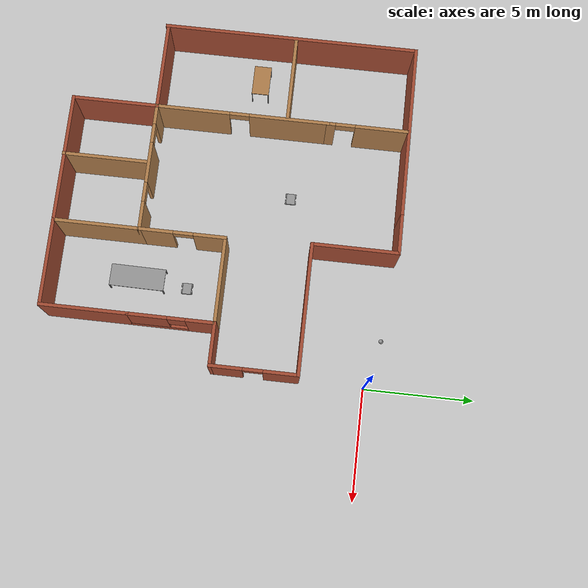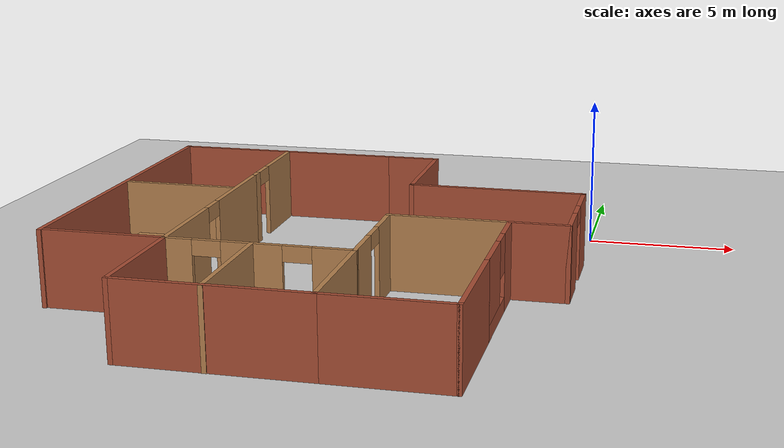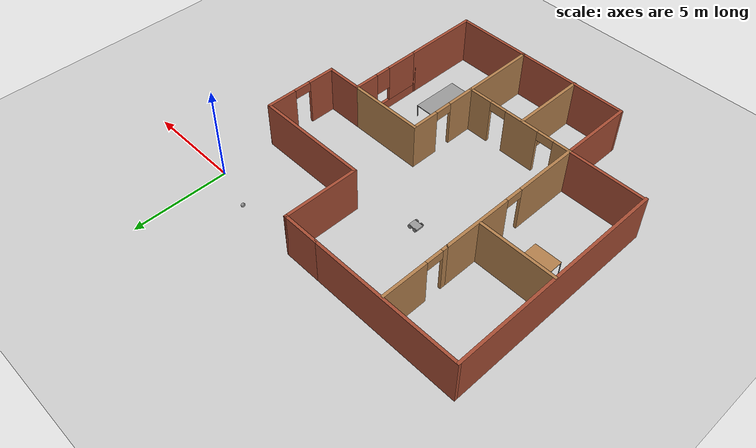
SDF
<sdf version="1.6">
 <world name="default">
  <plugin name="hello" filename="libhello.so"/>
  <light name="sun" type="directional">
   <pose>0 0 10 0 -0 0</pose>
   <diffuse>0.8 0.8 0.8 1</diffuse>
   <specular>0.1 0.1 0.1 1</specular>
   <attenuation>
    <range>1000</range>
    <constant>0.9</constant>
    <linear>0.01</linear>
    <quadratic>0.001</quadratic>
   </attenuation>
   <direction>-0.5 0.5 -1</direction>
  </light>
  <model name="ground_plane">
   <static>1</static>
   <link name="link">
    <collision name="collision">
     <geometry><plane><normal>0 0 1</normal><size>100 100</size></plane></geometry>
     <surface><friction><ode><mu>100</mu><mu2>50</mu2></ode></friction></surface>
    </collision>
    <visual name="visual">
     <cast_shadows>0</cast_shadows>
     <geometry><plane><normal>0 0 1</normal><size>100 100</size></plane></geometry>
     <material>
      <script><uri>file://media/materials/scripts/gazebo.material</uri><name>Gazebo/Grey</name></script>
     </material>
    </visual>
   </link>
  </model>
  <gravity>0 0 -9.8</gravity>
  <magnetic_field>6e-06 2.3e-05 -4.2e-05</magnetic_field>
  <atmosphere type="adiabatic"/>
  <physics name="default_physics" default="0" type="ode">
   <max_step_size>0.001</max_step_size>
   <real_time_factor>1</real_time_factor>
   <real_time_update_rate>1000</real_time_update_rate>
  </physics>
  <scene><ambient>0.4 0.4 0.4 1</ambient><background>0.7 0.7 0.7 1</background><shadows>1</shadows></scene>
  <spherical_coordinates>
   <surface_model>EARTH_WGS84</surface_model>
   <latitude_deg>0</latitude_deg>
   <longitude_deg>0</longitude_deg>
   <elevation>0</elevation>
   <heading_deg>0</heading_deg>
  </spherical_coordinates>
  <model name="Building">
   <pose>-7.76735 -6.83416 0 0 -0 0</pose>
   <link name="Wall_0">
    <collision name="Wall_0_Collision">
     <geometry><box><size>2 0.15 2.5</size></box></geometry>
     <pose>0 0 1.25 0 -0 0</pose>
    </collision>
    <visual name="Wall_0_Visual">
     <pose>0 0 1.25 0 -0 0</pose>
     <geometry><box><size>2 0.15 2.5</size></box></geometry>
     <material>
      <script><uri>file://media/materials/scripts/gazebo.material</uri><name>Gazebo/Bricks</name></script>
      <ambient>1 1 1 1</ambient>
     </material>
    </visual>
    <pose>1 7.71108 0 0 -0 0</pose>
   </link>
   <link name="Wall_1">
    <collision name="Wall_1_Collision">
     <geometry><box><size>4 0.15 2.5</size></box></geometry>
     <pose>0 0 1.25 0 -0 0</pose>
    </collision>
    <visual name="Wall_1_Visual">
     <pose>0 0 1.25 0 -0 0</pose>
     <geometry><box><size>4 0.15 2.5</size></box></geometry>
     <material>
      <script><uri>file://media/materials/scripts/gazebo.material</uri><name>Gazebo/Bricks</name></script>
      <ambient>1 1 1 1</ambient>
     </material>
    </visual>
    <pose>1.925 5.78608 0 0 0 -1.5708</pose>
   </link>
   <link name="Wall_10">
    <collision name="Wall_10_Collision">
     <geometry><box><size>6 0.15 2.5</size></box></geometry>
     <pose>0 0 1.25 0 -0 0</pose>
    </collision>
    <visual name="Wall_10_Visual">
     <pose>0 0 1.25 0 -0 0</pose>
     <geometry><box><size>6 0.15 2.5</size></box></geometry>
     <material>
      <script><uri>file://media/materials/scripts/gazebo.material</uri><name>Gazebo/Bricks</name></script>
      <ambient>1 1 1 1</ambient>
     </material>
    </visual>
    <pose>-0.849999 -7.68892 0 0 -0 3.14159</pose>
   </link>
   <link name="Wall_105">
    <collision name="Wall_105_Collision">
     <geometry><box><size>4 0.15 2.5</size></box></geometry>
     <pose>0 0 1.25 0 -0 0</pose>
    </collision>
    <visual name="Wall_105_Visual">
     <pose>0 0 1.25 0 -0 0</pose>
     <geometry><box><size>4 0.15 2.5</size></box></geometry>
     <material>
      <script><uri>file://media/materials/scripts/gazebo.material</uri><name>Gazebo/Wood</name></script>
      <ambient>0.760784 0.662745 0.627451 1</ambient>
     </material>
    </visual>
    <pose>2.075 -5.76392 0 0 0 -1.5708</pose>
   </link>
   <link name="Wall_109">
    <collision name="Wall_109_Collision">
     <geometry><box><size>4 0.15 2.5</size></box></geometry>
     <pose>0 0 1.25 0 -0 0</pose>
    </collision>
    <visual name="Wall_109_Visual">
     <pose>0 0 1.25 0 -0 0</pose>
     <geometry><box><size>4 0.15 2.5</size></box></geometry>
     <material>
      <script><uri>file://media/materials/scripts/gazebo.material</uri><name>Gazebo/Wood</name></script>
      <ambient>0.760784 0.662745 0.627451 1</ambient>
     </material>
    </visual>
    <pose>-1.05166 -5.78608 0 0 0 -1.5708</pose>
   </link>
   <link name="Wall_11">
    <collision name="Wall_11_Collision">
     <geometry><box><size>4 0.15 2.5</size></box></geometry>
     <pose>0 0 1.25 0 -0 0</pose>
    </collision>
    <visual name="Wall_11_Visual">
     <pose>0 0 1.25 0 -0 0</pose>
     <geometry><box><size>4 0.15 2.5</size></box></geometry>
     <material>
      <script><uri>file://media/materials/scripts/gazebo.material</uri><name>Gazebo/Bricks</name></script>
      <ambient>1 1 1 1</ambient>
     </material>
    </visual>
    <pose>-3.775 -5.76392 0 0 -0 1.5708</pose>
   </link>
   <link name="Wall_113">
    <pose>-3.775 5.81108 0 0 -0 1.5708</pose>
    <visual name="Wall_113_Visual_0">
     <pose>-1.66581 0 1.25 0 -0 0</pose>
     <geometry><box><size>0.418378 0.15 2.5</size></box></geometry>
     <material>
      <script><uri>file://media/materials/scripts/gazebo.material</uri><name>Gazebo/Wood</name></script>
      <ambient>0.435294 0.796078 0.67451 1</ambient>
     </material>
    </visual>
    <collision name="Wall_113_Collision_0">
     <geometry><box><size>0.418378 0.15 2.5</size></box></geometry>
     <pose>-1.66581 0 1.25 0 -0 0</pose>
    </collision>
    <visual name="Wall_113_Visual_1">
     <pose>0.659189 0 1.25 0 -0 0</pose>
     <geometry><box><size>2.43162 0.15 2.5</size></box></geometry>
     <material>
      <script><uri>file://media/materials/scripts/gazebo.material</uri><name>Gazebo/Wood</name></script>
      <ambient>0.435294 0.796078 0.67451 1</ambient>
     </material>
    </visual>
    <collision name="Wall_113_Collision_1">
     <geometry><box><size>2.43162 0.15 2.5</size></box></geometry>
     <pose>0.659189 0 1.25 0 -0 0</pose>
    </collision>
    <visual name="Wall_113_Visual_2">
     <pose>-1.00662 0 2.25 0 -0 0</pose>
     <geometry><box><size>0.9 0.15 0.5</size></box></geometry>
     <material>
      <script><uri>file://media/materials/scripts/gazebo.material</uri><name>Gazebo/Wood</name></script>
      <ambient>0.435294 0.796078 0.67451 1</ambient>
     </material>
    </visual>
    <collision name="Wall_113_Collision_2">
     <geometry><box><size>0.9 0.15 0.5</size></box></geometry>
     <pose>-1.00662 0 2.25 0 -0 0</pose>
    </collision>
   </link>
   <link name="Wall_115">
    <collision name="Wall_115_Collision">
     <geometry><box><size>4 0.15 2.5</size></box></geometry>
     <pose>0 0 1.25 0 -0 0</pose>
    </collision>
    <visual name="Wall_115_Visual">
     <pose>0 0 1.25 0 -0 0</pose>
     <geometry><box><size>4 0.15 2.5</size></box></geometry>
     <material>
      <script><uri>file://media/materials/scripts/gazebo.material</uri><name>Gazebo/Wood</name></script>
      <ambient>0.435294 0.796078 0.67451 1</ambient>
     </material>
    </visual>
    <pose>-5.82317 2.14798 0 0 -0 0</pose>
   </link>
   <link name="Wall_12">
    <collision name="Wall_12_Collision">
     <geometry><box><size>4 0.15 2.5</size></box></geometry>
     <pose>0 0 1.25 0 -0 0</pose>
    </collision>
    <visual name="Wall_12_Visual">
     <pose>0 0 1.25 0 -0 0</pose>
     <geometry><box><size>4 0.15 2.5</size></box></geometry>
     <material>
      <script><uri>file://media/materials/scripts/gazebo.material</uri><name>Gazebo/Bricks</name></script>
      <ambient>1 1 1 1</ambient>
     </material>
    </visual>
    <pose>-5.7 -3.83892 0 0 -0 3.14159</pose>
   </link>
   <link name="Wall_15">
    <collision name="Wall_15_Collision">
     <geometry><box><size>8 0.15 2.5</size></box></geometry>
     <pose>0 0 1.25 0 -0 0</pose>
    </collision>
    <visual name="Wall_15_Visual">
     <pose>0 0 1.25 0 -0 0</pose>
     <geometry><box><size>8 0.15 2.5</size></box></geometry>
     <material>
      <script><uri>file://media/materials/scripts/gazebo.material</uri><name>Gazebo/Bricks</name></script>
      <ambient>1 1 1 1</ambient>
     </material>
    </visual>
    <pose>-3.85 7.71108 0 0 -0 3.14159</pose>
   </link>
   <link name="Wall_16">
    <collision name="Wall_16_Collision">
     <geometry><box><size>11.75 0.15 2.5</size></box></geometry>
     <pose>0 0 1.25 0 -0 0</pose>
    </collision>
    <visual name="Wall_16_Visual">
     <pose>0 0 1.25 0 -0 0</pose>
     <geometry><box><size>11.75 0.15 2.5</size></box></geometry>
     <material>
      <script><uri>file://media/materials/scripts/gazebo.material</uri><name>Gazebo/Bricks</name></script>
      <ambient>1 1 1 1</ambient>
     </material>
    </visual>
    <pose>-7.775 1.91108 0 0 0 -1.5708</pose>
   </link>
   <link name="Wall_18">
    <pose>-0.849999 -3.83892 0 0 -0 0</pose>
    <visual name="Wall_18_Visual_0">
     <pose>-2.51905 0 1.25 0 -0 0</pose>
     <geometry><box><size>0.961894 0.15 2.5</size></box></geometry>
     <material>
      <script><uri>file://media/materials/scripts/gazebo.material</uri><name>Gazebo/Wood</name></script>
      <ambient>0.760784 0.662745 0.627451 1</ambient>
     </material>
    </visual>
    <collision name="Wall_18_Collision_0">
     <geometry><box><size>0.961894 0.15 2.5</size></box></geometry>
     <pose>-2.51905 0 1.25 0 -0 0</pose>
    </collision>
    <visual name="Wall_18_Visual_1">
     <pose>-0.191308 0 1.25 0 -0 0</pose>
     <geometry><box><size>1.8936 0.15 2.5</size></box></geometry>
     <material>
      <script><uri>file://media/materials/scripts/gazebo.material</uri><name>Gazebo/Wood</name></script>
      <ambient>0.760784 0.662745 0.627451 1</ambient>
     </material>
    </visual>
    <collision name="Wall_18_Collision_1">
     <geometry><box><size>1.8936 0.15 2.5</size></box></geometry>
     <pose>-0.191308 0 1.25 0 -0 0</pose>
    </collision>
    <visual name="Wall_18_Visual_2">
     <pose>2.32775 0 1.25 0 -0 0</pose>
     <geometry><box><size>1.34451 0.15 2.5</size></box></geometry>
     <material>
      <script><uri>file://media/materials/scripts/gazebo.material</uri><name>Gazebo/Wood</name></script>
      <ambient>0.760784 0.662745 0.627451 1</ambient>
     </material>
    </visual>
    <collision name="Wall_18_Collision_2">
     <geometry><box><size>1.34451 0.15 2.5</size></box></geometry>
     <pose>2.32775 0 1.25 0 -0 0</pose>
    </collision>
    <visual name="Wall_18_Visual_3">
     <pose>-1.58811 0 2.25 0 -0 0</pose>
     <geometry><box><size>0.9 0.15 0.5</size></box></geometry>
     <material>
      <script><uri>file://media/materials/scripts/gazebo.material</uri><name>Gazebo/Wood</name></script>
      <ambient>0.760784 0.662745 0.627451 1</ambient>
     </material>
    </visual>
    <collision name="Wall_18_Collision_3">
     <geometry><box><size>0.9 0.15 0.5</size></box></geometry>
     <pose>-1.58811 0 2.25 0 -0 0</pose>
    </collision>
    <visual name="Wall_18_Visual_4">
     <pose>1.20549 0 2.25 0 -0 0</pose>
     <geometry><box><size>0.9 0.15 0.5</size></box></geometry>
     <material>
      <script><uri>file://media/materials/scripts/gazebo.material</uri><name>Gazebo/Wood</name></script>
      <ambient>0.760784 0.662745 0.627451 1</ambient>
     </material>
    </visual>
    <collision name="Wall_18_Collision_4">
     <geometry><box><size>0.9 0.15 0.5</size></box></geometry>
     <pose>1.20549 0 2.25 0 -0 0</pose>
    </collision>
   </link>
   <link name="Wall_2">
    <collision name="Wall_2_Collision">
     <geometry><box><size>6 0.15 2.5</size></box></geometry>
     <pose>0 0 1.25 0 -0 0</pose>
    </collision>
    <visual name="Wall_2_Visual">
     <pose>0 0 1.25 0 -0 0</pose>
     <geometry><box><size>6 0.15 2.5</size></box></geometry>
     <material>
      <script><uri>file://media/materials/scripts/gazebo.material</uri><name>Gazebo/Bricks</name></script>
      <ambient>1 1 1 1</ambient>
     </material>
    </visual>
    <pose>4.85 3.86108 0 0 -0 0</pose>
   </link>
   <link name="Wall_20">
    <pose>-3.775 0.086083 0 0 -0 1.5708</pose>
    <visual name="Wall_20_Visual_0">
     <pose>-2.29315 0 1.25 0 -0 0</pose>
     <geometry><box><size>3.41371 0.15 2.5</size></box></geometry>
     <material>
      <script><uri>file://media/materials/scripts/gazebo.material</uri><name>Gazebo/Wood</name></script>
      <ambient>0.435294 0.796078 0.67451 1</ambient>
     </material>
    </visual>
    <collision name="Wall_20_Collision_0">
     <geometry><box><size>3.41371 0.15 2.5</size></box></geometry>
     <pose>-2.29315 0 1.25 0 -0 0</pose>
    </collision>
    <visual name="Wall_20_Visual_1">
     <pose>2.15685 0 1.25 0 -0 0</pose>
     <geometry><box><size>3.68629 0.15 2.5</size></box></geometry>
     <material>
      <script><uri>file://media/materials/scripts/gazebo.material</uri><name>Gazebo/Wood</name></script>
      <ambient>0.435294 0.796078 0.67451 1</ambient>
     </material>
    </visual>
    <collision name="Wall_20_Collision_1">
     <geometry><box><size>3.68629 0.15 2.5</size></box></geometry>
     <pose>2.15685 0 1.25 0 -0 0</pose>
    </collision>
    <visual name="Wall_20_Visual_2">
     <pose>-0.136292 0 2.25 0 -0 0</pose>
     <geometry><box><size>0.9 0.15 0.5</size></box></geometry>
     <material>
      <script><uri>file://media/materials/scripts/gazebo.material</uri><name>Gazebo/Wood</name></script>
      <ambient>0.435294 0.796078 0.67451 1</ambient>
     </material>
    </visual>
    <collision name="Wall_20_Collision_2">
     <geometry><box><size>0.9 0.15 0.5</size></box></geometry>
     <pose>-0.136292 0 2.25 0 -0 0</pose>
    </collision>
   </link>
   <link name="Wall_23">
    <pose>2.075 -1.91392 0 0 -0 1.5708</pose>
    <visual name="Wall_23_Visual_0">
     <pose>-1.20497 0 1.25 0 -0 0</pose>
     <geometry><box><size>1.59006 0.15 2.5</size></box></geometry>
     <material>
      <script><uri>file://media/materials/scripts/gazebo.material</uri><name>Gazebo/Wood</name></script>
      <ambient>0.760784 0.662745 0.627451 1</ambient>
     </material>
    </visual>
    <collision name="Wall_23_Collision_0">
     <geometry><box><size>1.59006 0.15 2.5</size></box></geometry>
     <pose>-1.20497 0 1.25 0 -0 0</pose>
    </collision>
    <visual name="Wall_23_Visual_1">
     <pose>1.24503 0 1.25 0 -0 0</pose>
     <geometry><box><size>1.50994 0.15 2.5</size></box></geometry>
     <material>
      <script><uri>file://media/materials/scripts/gazebo.material</uri><name>Gazebo/Wood</name></script>
      <ambient>0.760784 0.662745 0.627451 1</ambient>
     </material>
    </visual>
    <collision name="Wall_23_Collision_1">
     <geometry><box><size>1.50994 0.15 2.5</size></box></geometry>
     <pose>1.24503 0 1.25 0 -0 0</pose>
    </collision>
    <visual name="Wall_23_Visual_2">
     <pose>0.040062 0 2.25 0 -0 0</pose>
     <geometry><box><size>0.9 0.15 0.5</size></box></geometry>
     <material>
      <script><uri>file://media/materials/scripts/gazebo.material</uri><name>Gazebo/Wood</name></script>
      <ambient>0.760784 0.662745 0.627451 1</ambient>
     </material>
    </visual>
    <collision name="Wall_23_Collision_2">
     <geometry><box><size>0.9 0.15 0.5</size></box></geometry>
     <pose>0.040062 0 2.25 0 -0 0</pose>
    </collision>
   </link>
   <link name="Wall_24">
    <collision name="Wall_24_Collision">
     <geometry><box><size>4 0.15 2.5</size></box></geometry>
     <pose>0 0 1.25 0 -0 0</pose>
    </collision>
    <visual name="Wall_24_Visual">
     <pose>0 0 1.25 0 -0 0</pose>
     <geometry><box><size>4 0.15 2.5</size></box></geometry>
     <material>
      <script><uri>file://media/materials/scripts/gazebo.material</uri><name>Gazebo/Wood</name></script>
      <ambient>0.760784 0.662745 0.627451 1</ambient>
     </material>
    </visual>
    <pose>4 0.011084 0 0 -0 0</pose>
   </link>
   <link name="Wall_26">
    <collision name="Wall_26_Collision">
     <geometry><box><size>4 0.15 2.5</size></box></geometry>
     <pose>0 0 1.25 0 -0 0</pose>
    </collision>
    <visual name="Wall_26_Visual">
     <pose>0 0 1.25 0 -0 0</pose>
     <geometry><box><size>4 0.15 2.5</size></box></geometry>
     <material>
      <script><uri>file://media/materials/scripts/gazebo.material</uri><name>Gazebo/Bricks</name></script>
      <ambient>1 1 1 1</ambient>
     </material>
    </visual>
    <pose>4 -7.68892 0 0 -0 0</pose>
   </link>
   <link name="Wall_27">
    <collision name="Wall_27_Collision">
     <geometry><box><size>4 0.15 2.5</size></box></geometry>
     <pose>0 0 1.25 0 -0 0</pose>
    </collision>
    <visual name="Wall_27_Visual">
     <pose>0 0 1.25 0 -0 0</pose>
     <geometry><box><size>4 0.15 2.5</size></box></geometry>
     <material>
      <script><uri>file://media/materials/scripts/gazebo.material</uri><name>Gazebo/Bricks</name></script>
      <ambient>1 1 1 1</ambient>
     </material>
    </visual>
    <pose>5.925 -5.76392 0 0 -0 1.5708</pose>
   </link>
   <link name="Wall_3">
    <pose>7.775 1.93608 0 0 0 -1.5708</pose>
    <visual name="Wall_3_Visual_0">
     <pose>-1.19927 0 1.25 0 -0 0</pose>
     <geometry><box><size>1.60146 0.15 2.5</size></box></geometry>
     <material>
      <script><uri>file://media/materials/scripts/gazebo.material</uri><name>Gazebo/Bricks</name></script>
      <ambient>1 1 1 1</ambient>
     </material>
    </visual>
    <collision name="Wall_3_Collision_0">
     <geometry><box><size>1.60146 0.15 2.5</size></box></geometry>
     <pose>-1.19927 0 1.25 0 -0 0</pose>
    </collision>
    <visual name="Wall_3_Visual_1">
     <pose>1.25073 0 1.25 0 -0 0</pose>
     <geometry><box><size>1.49854 0.15 2.5</size></box></geometry>
     <material>
      <script><uri>file://media/materials/scripts/gazebo.material</uri><name>Gazebo/Bricks</name></script>
      <ambient>1 1 1 1</ambient>
     </material>
    </visual>
    <collision name="Wall_3_Collision_1">
     <geometry><box><size>1.49854 0.15 2.5</size></box></geometry>
     <pose>1.25073 0 1.25 0 -0 0</pose>
    </collision>
    <visual name="Wall_3_Visual_2">
     <pose>0.051459 0 2.25 0 -0 0</pose>
     <geometry><box><size>0.9 0.15 0.5</size></box></geometry>
     <material>
      <script><uri>file://media/materials/scripts/gazebo.material</uri><name>Gazebo/Bricks</name></script>
      <ambient>1 1 1 1</ambient>
     </material>
    </visual>
    <collision name="Wall_3_Collision_2">
     <geometry><box><size>0.9 0.15 0.5</size></box></geometry>
     <pose>0.051459 0 2.25 0 -0 0</pose>
    </collision>
   </link>
   <link name="Wall_4">
    <collision name="Wall_4_Collision">
     <geometry><box><size>2 0.15 2.5</size></box></geometry>
     <pose>0 0 1.25 0 -0 0</pose>
    </collision>
    <visual name="Wall_4_Visual">
     <pose>0 0 1.25 0 -0 0</pose>
     <geometry><box><size>2 0.15 2.5</size></box></geometry>
     <material>
      <script><uri>file://media/materials/scripts/gazebo.material</uri><name>Gazebo/Bricks</name></script>
      <ambient>1 1 1 1</ambient>
     </material>
    </visual>
    <pose>6.85 0.011084 0 0 -0 3.14159</pose>
   </link>
   <link name="Wall_6">
    <pose>5.925 -1.91392 0 0 0 -1.5708</pose>
    <visual name="Wall_6_Visual_0">
     <pose>-1.31823 0 1.25 0 -0 0</pose>
     <geometry><box><size>1.36353 0.15 2.5</size></box></geometry>
     <material>
      <script><uri>file://media/materials/scripts/gazebo.material</uri><name>Gazebo/Bricks</name></script>
      <ambient>1 1 1 1</ambient>
     </material>
    </visual>
    <collision name="Wall_6_Collision_0">
     <geometry><box><size>1.36353 0.15 2.5</size></box></geometry>
     <pose>-1.31823 0 1.25 0 -0 0</pose>
    </collision>
    <visual name="Wall_6_Visual_1">
     <pose>0.681767 0 0.25 0 -0 0</pose>
     <geometry><box><size>2.63647 0.15 0.5</size></box></geometry>
     <material>
      <script><uri>file://media/materials/scripts/gazebo.material</uri><name>Gazebo/Bricks</name></script>
      <ambient>1 1 1 1</ambient>
     </material>
    </visual>
    <collision name="Wall_6_Collision_1">
     <geometry><box><size>2.63647 0.15 0.5</size></box></geometry>
     <pose>0.681767 0 0.25 0 -0 0</pose>
    </collision>
    <visual name="Wall_6_Visual_2">
     <pose>1.08177 0 1.5 0 -0 0</pose>
     <geometry><box><size>1.83647 0.15 2</size></box></geometry>
     <material>
      <script><uri>file://media/materials/scripts/gazebo.material</uri><name>Gazebo/Bricks</name></script>
      <ambient>1 1 1 1</ambient>
     </material>
    </visual>
    <collision name="Wall_6_Collision_2">
     <geometry><box><size>1.83647 0.15 2</size></box></geometry>
     <pose>1.08177 0 1.5 0 -0 0</pose>
    </collision>
    <visual name="Wall_6_Visual_3">
     <pose>-0.236466 0 1.9 0 -0 0</pose>
     <geometry><box><size>0.8 0.15 1.2</size></box></geometry>
     <material>
      <script><uri>file://media/materials/scripts/gazebo.material</uri><name>Gazebo/Bricks</name></script>
      <ambient>1 1 1 1</ambient>
     </material>
    </visual>
    <collision name="Wall_6_Collision_3">
     <geometry><box><size>0.8 0.15 1.2</size></box></geometry>
     <pose>-0.236466 0 1.9 0 -0 0</pose>
    </collision>
   </link>
   <static>1</static>
  </model>
  <model name="2.5x1_table">
   <link name="link_0">
    <pose>0 0 0.264 0 -0 0</pose>
    <inertial>
     <mass>1</mass>
     <inertia>
      <ixx>0.166667</ixx>
      <ixy>0</ixy>
      <ixz>0</ixz>
      <iyy>0.166667</iyy>
      <iyz>0</iyz>
      <izz>0.166667</izz>
     </inertia>
    </inertial>
    <visual name="visual">
     <geometry><box><size>2.5 1 0.04</size></box></geometry>
     <material>
      <lighting>1</lighting>
      <script><uri>file://media/materials/scripts/gazebo.material</uri><name>Gazebo/Grey</name></script>
      <ambient>0.3 0.3 0.3 1</ambient>
      <diffuse>0.7 0.7 0.7 1</diffuse>
      <specular>0.01 0.01 0.01 1</specular>
      <emissive>0 0 0 1</emissive>
      <shader type="vertex"><normal_map>__default__</normal_map></shader>
     </material>
    </visual>
    <collision name="collision">
     <geometry><box><size>2.5 1 0.04</size></box></geometry>
     <surface>
      <friction>
       <ode><mu>1</mu><mu2>1</mu2><fdir1>0 0 0</fdir1><slip1>0</slip1><slip2>0</slip2></ode>
       <torsional>
        <coefficient>1</coefficient>
        <patch_radius>0</patch_radius>
        <surface_radius>0</surface_radius>
        <use_patch_radius>1</use_patch_radius>
        <ode><slip>0</slip></ode>
       </torsional>
      </friction>
      <bounce><restitution_coefficient>0</restitution_coefficient><threshold>1e+06</threshold></bounce>
      <contact>
       <collide_without_contact>0</collide_without_contact>
       <collide_without_contact_bitmask>1</collide_without_contact_bitmask>
       <collide_bitmask>1</collide_bitmask>
       <ode>
        <soft_cfm>0</soft_cfm>
        <soft_erp>0.2</soft_erp>
        <kp>1e+13</kp>
        <kd>1</kd>
        <max_vel>0.01</max_vel>
        <min_depth>0</min_depth>
       </ode>
       <bullet>
        <split_impulse>1</split_impulse>
        <split_impulse_penetration_threshold>-0.01</split_impulse_penetration_threshold>
        <soft_cfm>0</soft_cfm>
        <soft_erp>0.2</soft_erp>
        <kp>1e+13</kp>
        <kd>1</kd>
       </bullet>
      </contact>
     </surface>
    </collision>
   </link>
   <link name="link_1">
    <pose>-1.23 -0.48 -0.066 0 -0 0</pose>
    <inertial>
     <mass>1</mass>
     <inertia>
      <ixx>0.166667</ixx>
      <ixy>0</ixy>
      <ixz>0</ixz>
      <iyy>0.166667</iyy>
      <iyz>0</iyz>
      <izz>0.166667</izz>
     </inertia>
    </inertial>
    <visual name="visual">
     <geometry><box><size>0.04 0.04 0.7</size></box></geometry>
     <material>
      <lighting>1</lighting>
      <script><uri>file://media/materials/scripts/gazebo.material</uri><name>Gazebo/Grey</name></script>
      <ambient>0.3 0.3 0.3 1</ambient>
      <diffuse>0.7 0.7 0.7 1</diffuse>
      <specular>0.01 0.01 0.01 1</specular>
      <emissive>0 0 0 1</emissive>
      <shader type="vertex"><normal_map>__default__</normal_map></shader>
     </material>
    </visual>
    <collision name="collision">
     <geometry><box><size>0.04 0.04 0.7</size></box></geometry>
     <surface>
      <friction>
       <ode><mu>1</mu><mu2>1</mu2><fdir1>0 0 0</fdir1><slip1>0</slip1><slip2>0</slip2></ode>
       <torsional>
        <coefficient>1</coefficient>
        <patch_radius>0</patch_radius>
        <surface_radius>0</surface_radius>
        <use_patch_radius>1</use_patch_radius>
        <ode><slip>0</slip></ode>
       </torsional>
      </friction>
      <bounce><restitution_coefficient>0</restitution_coefficient><threshold>1e+06</threshold></bounce>
      <contact>
       <collide_without_contact>0</collide_without_contact>
       <collide_without_contact_bitmask>1</collide_without_contact_bitmask>
       <collide_bitmask>1</collide_bitmask>
       <ode>
        <soft_cfm>0</soft_cfm>
        <soft_erp>0.2</soft_erp>
        <kp>1e+13</kp>
        <kd>1</kd>
        <max_vel>0.01</max_vel>
        <min_depth>0</min_depth>
       </ode>
       <bullet>
        <split_impulse>1</split_impulse>
        <split_impulse_penetration_threshold>-0.01</split_impulse_penetration_threshold>
        <soft_cfm>0</soft_cfm>
        <soft_erp>0.2</soft_erp>
        <kp>1e+13</kp>
        <kd>1</kd>
       </bullet>
      </contact>
     </surface>
    </collision>
   </link>
   <link name="link_1_clone">
    <pose>-1.23 0.48 -0.066 0 -0 0</pose>
    <inertial>
     <mass>1</mass>
     <inertia>
      <ixx>0.166667</ixx>
      <ixy>0</ixy>
      <ixz>0</ixz>
      <iyy>0.166667</iyy>
      <iyz>0</iyz>
      <izz>0.166667</izz>
     </inertia>
    </inertial>
    <visual name="visual">
     <geometry><box><size>0.04 0.04 0.7</size></box></geometry>
     <material>
      <lighting>1</lighting>
      <script><uri>file://media/materials/scripts/gazebo.material</uri><name>Gazebo/Grey</name></script>
      <ambient>0.3 0.3 0.3 1</ambient>
      <diffuse>0.7 0.7 0.7 1</diffuse>
      <specular>0.01 0.01 0.01 1</specular>
      <emissive>0 0 0 1</emissive>
      <shader type="vertex"><normal_map>__default__</normal_map></shader>
     </material>
    </visual>
    <collision name="collision">
     <geometry><box><size>0.04 0.04 0.7</size></box></geometry>
     <surface>
      <friction>
       <ode><mu>1</mu><mu2>1</mu2><fdir1>0 0 0</fdir1><slip1>0</slip1><slip2>0</slip2></ode>
       <torsional>
        <coefficient>1</coefficient>
        <patch_radius>0</patch_radius>
        <surface_radius>0</surface_radius>
        <use_patch_radius>1</use_patch_radius>
        <ode><slip>0</slip></ode>
       </torsional>
      </friction>
      <bounce><restitution_coefficient>0</restitution_coefficient><threshold>1e+06</threshold></bounce>
      <contact>
       <collide_without_contact>0</collide_without_contact>
       <collide_without_contact_bitmask>1</collide_without_contact_bitmask>
       <collide_bitmask>1</collide_bitmask>
       <ode>
        <soft_cfm>0</soft_cfm>
        <soft_erp>0.2</soft_erp>
        <kp>1e+13</kp>
        <kd>1</kd>
        <max_vel>0.01</max_vel>
        <min_depth>0</min_depth>
       </ode>
       <bullet>
        <split_impulse>1</split_impulse>
        <split_impulse_penetration_threshold>-0.01</split_impulse_penetration_threshold>
        <soft_cfm>0</soft_cfm>
        <soft_erp>0.2</soft_erp>
        <kp>1e+13</kp>
        <kd>1</kd>
       </bullet>
      </contact>
     </surface>
    </collision>
   </link>
   <link name="link_1_clone_0">
    <pose>1.23 0.48 -0.066 0 -0 0</pose>
    <inertial>
     <mass>1</mass>
     <inertia>
      <ixx>0.166667</ixx>
      <ixy>0</ixy>
      <ixz>0</ixz>
      <iyy>0.166667</iyy>
      <iyz>0</iyz>
      <izz>0.166667</izz>
     </inertia>
    </inertial>
    <visual name="visual">
     <geometry><box><size>0.04 0.04 0.7</size></box></geometry>
     <material>
      <lighting>1</lighting>
      <script><uri>file://media/materials/scripts/gazebo.material</uri><name>Gazebo/Grey</name></script>
      <ambient>0.3 0.3 0.3 1</ambient>
      <diffuse>0.7 0.7 0.7 1</diffuse>
      <specular>0.01 0.01 0.01 1</specular>
      <emissive>0 0 0 1</emissive>
      <shader type="vertex"><normal_map>__default__</normal_map></shader>
     </material>
    </visual>
    <collision name="collision">
     <geometry><box><size>0.04 0.04 0.7</size></box></geometry>
     <surface>
      <friction>
       <ode><mu>1</mu><mu2>1</mu2><fdir1>0 0 0</fdir1><slip1>0</slip1><slip2>0</slip2></ode>
       <torsional>
        <coefficient>1</coefficient>
        <patch_radius>0</patch_radius>
        <surface_radius>0</surface_radius>
        <use_patch_radius>1</use_patch_radius>
        <ode><slip>0</slip></ode>
       </torsional>
      </friction>
      <bounce><restitution_coefficient>0</restitution_coefficient><threshold>1e+06</threshold></bounce>
      <contact>
       <collide_without_contact>0</collide_without_contact>
       <collide_without_contact_bitmask>1</collide_without_contact_bitmask>
       <collide_bitmask>1</collide_bitmask>
       <ode>
        <soft_cfm>0</soft_cfm>
        <soft_erp>0.2</soft_erp>
        <kp>1e+13</kp>
        <kd>1</kd>
        <max_vel>0.01</max_vel>
        <min_depth>0</min_depth>
       </ode>
       <bullet>
        <split_impulse>1</split_impulse>
        <split_impulse_penetration_threshold>-0.01</split_impulse_penetration_threshold>
        <soft_cfm>0</soft_cfm>
        <soft_erp>0.2</soft_erp>
        <kp>1e+13</kp>
        <kd>1</kd>
       </bullet>
      </contact>
     </surface>
    </collision>
   </link>
   <link name="link_1_clone_1">
    <pose>1.23 -0.48 -0.066 0 -0 0</pose>
    <inertial>
     <mass>1</mass>
     <inertia>
      <ixx>0.166667</ixx>
      <ixy>0</ixy>
      <ixz>0</ixz>
      <iyy>0.166667</iyy>
      <iyz>0</iyz>
      <izz>0.166667</izz>
     </inertia>
    </inertial>
    <visual name="visual">
     <geometry><box><size>0.04 0.04 0.7</size></box></geometry>
     <material>
      <lighting>1</lighting>
      <script><uri>file://media/materials/scripts/gazebo.material</uri><name>Gazebo/Grey</name></script>
      <ambient>0.3 0.3 0.3 1</ambient>
      <diffuse>0.7 0.7 0.7 1</diffuse>
      <specular>0.01 0.01 0.01 1</specular>
      <emissive>0 0 0 1</emissive>
      <shader type="vertex"><normal_map>__default__</normal_map></shader>
     </material>
    </visual>
    <collision name="collision">
     <geometry><box><size>0.04 0.04 0.7</size></box></geometry>
     <surface>
      <friction>
       <ode><mu>1</mu><mu2>1</mu2><fdir1>0 0 0</fdir1><slip1>0</slip1><slip2>0</slip2></ode>
       <torsional>
        <coefficient>1</coefficient>
        <patch_radius>0</patch_radius>
        <surface_radius>0</surface_radius>
        <use_patch_radius>1</use_patch_radius>
        <ode><slip>0</slip></ode>
       </torsional>
      </friction>
      <bounce><restitution_coefficient>0</restitution_coefficient><threshold>1e+06</threshold></bounce>
      <contact>
       <collide_without_contact>0</collide_without_contact>
       <collide_without_contact_bitmask>1</collide_without_contact_bitmask>
       <collide_bitmask>1</collide_bitmask>
       <ode>
        <soft_cfm>0</soft_cfm>
        <soft_erp>0.2</soft_erp>
        <kp>1e+13</kp>
        <kd>1</kd>
        <max_vel>0.01</max_vel>
        <min_depth>0</min_depth>
       </ode>
       <bullet>
        <split_impulse>1</split_impulse>
        <split_impulse_penetration_threshold>-0.01</split_impulse_penetration_threshold>
        <soft_cfm>0</soft_cfm>
        <soft_erp>0.2</soft_erp>
        <kp>1e+13</kp>
        <kd>1</kd>
       </bullet>
      </contact>
     </surface>
    </collision>
   </link>
   <joint name="link_0_JOINT_0" type="revolute">
    <parent>link_0</parent>
    <child>link_1</child>
    <axis>
     <xyz>1 0 0</xyz>
     <use_parent_model_frame>0</use_parent_model_frame>
     <limit>
      <lower>-1.79769e+308</lower>
      <upper>1.79769e+308</upper>
      <effort>-1</effort>
      <velocity>-1</velocity>
     </limit>
     <dynamics>
      <spring_reference>0</spring_reference>
      <spring_stiffness>0</spring_stiffness>
      <damping>0</damping>
     </dynamics>
    </axis>
    <physics>
     <ode><limit><cfm>0</cfm><erp>0.2</erp></limit><suspension><cfm>0</cfm><erp>0.2</erp></suspension></ode>
    </physics>
   </joint>
   <joint name="link_0_JOINT_1" type="revolute">
    <parent>link_0</parent>
    <child>link_1_clone</child>
    <axis>
     <xyz>1 0 0</xyz>
     <use_parent_model_frame>0</use_parent_model_frame>
     <limit>
      <lower>-1.79769e+308</lower>
      <upper>1.79769e+308</upper>
      <effort>-1</effort>
      <velocity>-1</velocity>
     </limit>
     <dynamics>
      <spring_reference>0</spring_reference>
      <spring_stiffness>0</spring_stiffness>
      <damping>0</damping>
     </dynamics>
    </axis>
    <physics>
     <ode><limit><cfm>0</cfm><erp>0.2</erp></limit><suspension><cfm>0</cfm><erp>0.2</erp></suspension></ode>
    </physics>
   </joint>
   <joint name="link_0_JOINT_2" type="revolute">
    <parent>link_0</parent>
    <child>link_1_clone_0</child>
    <axis>
     <xyz>1 0 0</xyz>
     <use_parent_model_frame>0</use_parent_model_frame>
     <limit>
      <lower>-1.79769e+308</lower>
      <upper>1.79769e+308</upper>
      <effort>-1</effort>
      <velocity>-1</velocity>
     </limit>
     <dynamics>
      <spring_reference>0</spring_reference>
      <spring_stiffness>0</spring_stiffness>
      <damping>0</damping>
     </dynamics>
    </axis>
    <physics>
     <ode><limit><cfm>0</cfm><erp>0.2</erp></limit><suspension><cfm>0</cfm><erp>0.2</erp></suspension></ode>
    </physics>
   </joint>
   <joint name="link_0_JOINT_3" type="revolute">
    <parent>link_0</parent>
    <child>link_1_clone_1</child>
    <axis>
     <xyz>1 0 0</xyz>
     <use_parent_model_frame>0</use_parent_model_frame>
     <limit>
      <lower>-1.79769e+308</lower>
      <upper>1.79769e+308</upper>
      <effort>-1</effort>
      <velocity>-1</velocity>
     </limit>
     <dynamics>
      <spring_reference>0</spring_reference>
      <spring_stiffness>0</spring_stiffness>
      <damping>0</damping>
     </dynamics>
    </axis>
    <physics>
     <ode><limit><cfm>0</cfm><erp>0.2</erp></limit><suspension><cfm>0</cfm><erp>0.2</erp></suspension></ode>
    </physics>
   </joint>
   <static>0</static>
   <pose>-3.86398 -10.7104 0.415995 3.4e-05 9e-06 -1.58021</pose>
  </model>
  <model name="Car">
   <link name="link_0">
    <inertial>
     <mass>1</mass>
     <inertia>
      <ixx>0.166667</ixx>
      <ixy>0</ixy>
      <ixz>0</ixz>
      <iyy>0.166667</iyy>
      <iyz>0</iyz>
      <izz>0.166667</izz>
     </inertia>
    </inertial>
    <visual name="visual">
     <geometry><box><size>0.5 0.4 0.1</size></box></geometry>
     <material>
      <lighting>1</lighting>
      <script><uri>file://media/materials/scripts/gazebo.material</uri><name>Gazebo/Grey</name></script>
      <ambient>0.3 0.3 0.3 1</ambient>
      <diffuse>0.7 0.7 0.7 1</diffuse>
      <specular>0.01 0.01 0.01 1</specular>
      <emissive>0 0 0 1</emissive>
      <shader type="vertex"><normal_map>__default__</normal_map></shader>
     </material>
    </visual>
    <collision name="collision">
     <geometry><box><size>0.5 0.4 0.1</size></box></geometry>
     <surface>
      <friction>
       <ode><mu>1</mu><mu2>1</mu2><fdir1>0 0 0</fdir1><slip1>0</slip1><slip2>0</slip2></ode>
       <torsional>
        <coefficient>1</coefficient>
        <patch_radius>0</patch_radius>
        <surface_radius>0</surface_radius>
        <use_patch_radius>1</use_patch_radius>
        <ode><slip>0</slip></ode>
       </torsional>
      </friction>
      <bounce><restitution_coefficient>0</restitution_coefficient><threshold>1e+06</threshold></bounce>
      <contact>
       <collide_without_contact>0</collide_without_contact>
       <collide_without_contact_bitmask>1</collide_without_contact_bitmask>
       <collide_bitmask>1</collide_bitmask>
       <ode>
        <soft_cfm>0</soft_cfm>
        <soft_erp>0.2</soft_erp>
        <kp>1e+13</kp>
        <kd>1</kd>
        <max_vel>0.01</max_vel>
        <min_depth>0</min_depth>
       </ode>
       <bullet>
        <split_impulse>1</split_impulse>
        <split_impulse_penetration_threshold>-0.01</split_impulse_penetration_threshold>
        <soft_cfm>0</soft_cfm>
        <soft_erp>0.2</soft_erp>
        <kp>1e+13</kp>
        <kd>1</kd>
       </bullet>
      </contact>
     </surface>
    </collision>
   </link>
   <link name="link_1">
    <pose>-0.15 -0.22501 0 1.5707 -0 0</pose>
    <inertial>
     <mass>1</mass>
     <inertia><ixx>0.145833</ixx><ixy>0</ixy><ixz>0</ixz><iyy>0.145833</iyy><iyz>0</iyz><izz>0.125</izz></inertia>
    </inertial>
    <visual name="visual">
     <geometry><cylinder><radius>0.1</radius><length>0.05</length></cylinder></geometry>
     <material>
      <lighting>1</lighting>
      <script><uri>file://media/materials/scripts/gazebo.material</uri><name>Gazebo/Grey</name></script>
      <ambient>0.3 0.3 0.3 1</ambient>
      <diffuse>0.7 0.7 0.7 1</diffuse>
      <specular>0.01 0.01 0.01 1</specular>
      <emissive>0 0 0 1</emissive>
      <shader type="vertex"><normal_map>__default__</normal_map></shader>
     </material>
    </visual>
    <collision name="collision">
     <geometry><cylinder><radius>0.1</radius><length>0.05</length></cylinder></geometry>
     <surface>
      <friction>
       <ode><mu>1</mu><mu2>1</mu2><fdir1>0 0 0</fdir1><slip1>0</slip1><slip2>0</slip2></ode>
       <torsional>
        <coefficient>1</coefficient>
        <patch_radius>0</patch_radius>
        <surface_radius>0</surface_radius>
        <use_patch_radius>1</use_patch_radius>
        <ode><slip>0</slip></ode>
       </torsional>
      </friction>
      <bounce><restitution_coefficient>0</restitution_coefficient><threshold>1e+06</threshold></bounce>
      <contact>
       <collide_without_contact>0</collide_without_contact>
       <collide_without_contact_bitmask>1</collide_without_contact_bitmask>
       <collide_bitmask>1</collide_bitmask>
       <ode>
        <soft_cfm>0</soft_cfm>
        <soft_erp>0.2</soft_erp>
        <kp>1e+13</kp>
        <kd>1</kd>
        <max_vel>0.01</max_vel>
        <min_depth>0</min_depth>
       </ode>
       <bullet>
        <split_impulse>1</split_impulse>
        <split_impulse_penetration_threshold>-0.01</split_impulse_penetration_threshold>
        <soft_cfm>0</soft_cfm>
        <soft_erp>0.2</soft_erp>
        <kp>1e+13</kp>
        <kd>1</kd>
       </bullet>
      </contact>
     </surface>
    </collision>
   </link>
   <link name="link_1_clone">
    <pose>-0.15 0.22501 0 1.5707 -0 0</pose>
    <inertial>
     <mass>1</mass>
     <inertia><ixx>0.145833</ixx><ixy>0</ixy><ixz>0</ixz><iyy>0.145833</iyy><iyz>0</iyz><izz>0.125</izz></inertia>
    </inertial>
    <visual name="visual">
     <geometry><cylinder><radius>0.1</radius><length>0.05</length></cylinder></geometry>
     <material>
      <lighting>1</lighting>
      <script><uri>file://media/materials/scripts/gazebo.material</uri><name>Gazebo/Grey</name></script>
      <ambient>0.3 0.3 0.3 1</ambient>
      <diffuse>0.7 0.7 0.7 1</diffuse>
      <specular>0.01 0.01 0.01 1</specular>
      <emissive>0 0 0 1</emissive>
      <shader type="vertex"><normal_map>__default__</normal_map></shader>
     </material>
    </visual>
    <collision name="collision">
     <geometry><cylinder><radius>0.1</radius><length>0.05</length></cylinder></geometry>
     <surface>
      <friction>
       <ode><mu>1</mu><mu2>1</mu2><fdir1>0 0 0</fdir1><slip1>0</slip1><slip2>0</slip2></ode>
       <torsional>
        <coefficient>1</coefficient>
        <patch_radius>0</patch_radius>
        <surface_radius>0</surface_radius>
        <use_patch_radius>1</use_patch_radius>
        <ode><slip>0</slip></ode>
       </torsional>
      </friction>
      <bounce><restitution_coefficient>0</restitution_coefficient><threshold>1e+06</threshold></bounce>
      <contact>
       <collide_without_contact>0</collide_without_contact>
       <collide_without_contact_bitmask>1</collide_without_contact_bitmask>
       <collide_bitmask>1</collide_bitmask>
       <ode>
        <soft_cfm>0</soft_cfm>
        <soft_erp>0.2</soft_erp>
        <kp>1e+13</kp>
        <kd>1</kd>
        <max_vel>0.01</max_vel>
        <min_depth>0</min_depth>
       </ode>
       <bullet>
        <split_impulse>1</split_impulse>
        <split_impulse_penetration_threshold>-0.01</split_impulse_penetration_threshold>
        <soft_cfm>0</soft_cfm>
        <soft_erp>0.2</soft_erp>
        <kp>1e+13</kp>
        <kd>1</kd>
       </bullet>
      </contact>
     </surface>
    </collision>
   </link>
   <link name="link_1_clone_0">
    <pose>0.15 -0.22501 0 1.5707 -0 0</pose>
    <inertial>
     <mass>1</mass>
     <inertia><ixx>0.145833</ixx><ixy>0</ixy><ixz>0</ixz><iyy>0.145833</iyy><iyz>0</iyz><izz>0.125</izz></inertia>
    </inertial>
    <visual name="visual">
     <geometry><cylinder><radius>0.1</radius><length>0.05</length></cylinder></geometry>
     <material>
      <lighting>1</lighting>
      <script><uri>file://media/materials/scripts/gazebo.material</uri><name>Gazebo/Grey</name></script>
      <ambient>0.3 0.3 0.3 1</ambient>
      <diffuse>0.7 0.7 0.7 1</diffuse>
      <specular>0.01 0.01 0.01 1</specular>
      <emissive>0 0 0 1</emissive>
      <shader type="vertex"><normal_map>__default__</normal_map></shader>
     </material>
    </visual>
    <collision name="collision">
     <geometry><cylinder><radius>0.1</radius><length>0.05</length></cylinder></geometry>
     <surface>
      <friction>
       <ode><mu>1</mu><mu2>1</mu2><fdir1>0 0 0</fdir1><slip1>0</slip1><slip2>0</slip2></ode>
       <torsional>
        <coefficient>1</coefficient>
        <patch_radius>0</patch_radius>
        <surface_radius>0</surface_radius>
        <use_patch_radius>1</use_patch_radius>
        <ode><slip>0</slip></ode>
       </torsional>
      </friction>
      <bounce><restitution_coefficient>0</restitution_coefficient><threshold>1e+06</threshold></bounce>
      <contact>
       <collide_without_contact>0</collide_without_contact>
       <collide_without_contact_bitmask>1</collide_without_contact_bitmask>
       <collide_bitmask>1</collide_bitmask>
       <ode>
        <soft_cfm>0</soft_cfm>
        <soft_erp>0.2</soft_erp>
        <kp>1e+13</kp>
        <kd>1</kd>
        <max_vel>0.01</max_vel>
        <min_depth>0</min_depth>
       </ode>
       <bullet>
        <split_impulse>1</split_impulse>
        <split_impulse_penetration_threshold>-0.01</split_impulse_penetration_threshold>
        <soft_cfm>0</soft_cfm>
        <soft_erp>0.2</soft_erp>
        <kp>1e+13</kp>
        <kd>1</kd>
       </bullet>
      </contact>
     </surface>
    </collision>
   </link>
   <link name="link_1_clone_1">
    <pose>0.15 0.22501 0 1.5707 -0 0</pose>
    <inertial>
     <mass>1</mass>
     <inertia><ixx>0.145833</ixx><ixy>0</ixy><ixz>0</ixz><iyy>0.145833</iyy><iyz>0</iyz><izz>0.125</izz></inertia>
    </inertial>
    <visual name="visual">
     <geometry><cylinder><radius>0.1</radius><length>0.05</length></cylinder></geometry>
     <material>
      <lighting>1</lighting>
      <script><uri>file://media/materials/scripts/gazebo.material</uri><name>Gazebo/Grey</name></script>
      <ambient>0.3 0.3 0.3 1</ambient>
      <diffuse>0.7 0.7 0.7 1</diffuse>
      <specular>0.01 0.01 0.01 1</specular>
      <emissive>0 0 0 1</emissive>
      <shader type="vertex"><normal_map>__default__</normal_map></shader>
     </material>
    </visual>
    <collision name="collision">
     <geometry><cylinder><radius>0.1</radius><length>0.05</length></cylinder></geometry>
     <surface>
      <friction>
       <ode><mu>1</mu><mu2>1</mu2><fdir1>0 0 0</fdir1><slip1>0</slip1><slip2>0</slip2></ode>
       <torsional>
        <coefficient>1</coefficient>
        <patch_radius>0</patch_radius>
        <surface_radius>0</surface_radius>
        <use_patch_radius>1</use_patch_radius>
        <ode><slip>0</slip></ode>
       </torsional>
      </friction>
      <bounce><restitution_coefficient>0</restitution_coefficient><threshold>1e+06</threshold></bounce>
      <contact>
       <collide_without_contact>0</collide_without_contact>
       <collide_without_contact_bitmask>1</collide_without_contact_bitmask>
       <collide_bitmask>1</collide_bitmask>
       <ode>
        <soft_cfm>0</soft_cfm>
        <soft_erp>0.2</soft_erp>
        <kp>1e+13</kp>
        <kd>1</kd>
        <max_vel>0.01</max_vel>
        <min_depth>0</min_depth>
       </ode>
       <bullet>
        <split_impulse>1</split_impulse>
        <split_impulse_penetration_threshold>-0.01</split_impulse_penetration_threshold>
        <soft_cfm>0</soft_cfm>
        <soft_erp>0.2</soft_erp>
        <kp>1e+13</kp>
        <kd>1</kd>
       </bullet>
      </contact>
     </surface>
    </collision>
   </link>
   <joint name="link_0_JOINT_0" type="revolute">
    <parent>link_0</parent>
    <child>link_1</child>
    <axis>
     <xyz>1 0 0</xyz>
     <use_parent_model_frame>0</use_parent_model_frame>
     <limit>
      <lower>-1.79769e+308</lower>
      <upper>1.79769e+308</upper>
      <effort>-1</effort>
      <velocity>-1</velocity>
     </limit>
     <dynamics>
      <spring_reference>0</spring_reference>
      <spring_stiffness>0</spring_stiffness>
      <damping>0</damping>
     </dynamics>
    </axis>
    <physics>
     <ode><limit><cfm>0</cfm><erp>0.2</erp></limit><suspension><cfm>0</cfm><erp>0.2</erp></suspension></ode>
    </physics>
   </joint>
   <joint name="link_0_JOINT_1" type="revolute">
    <parent>link_0</parent>
    <child>link_1</child>
    <axis>
     <xyz>1 0 0</xyz>
     <use_parent_model_frame>0</use_parent_model_frame>
     <limit>
      <lower>-1.79769e+308</lower>
      <upper>1.79769e+308</upper>
      <effort>-1</effort>
      <velocity>-1</velocity>
     </limit>
     <dynamics>
      <spring_reference>0</spring_reference>
      <spring_stiffness>0</spring_stiffness>
      <damping>0</damping>
     </dynamics>
    </axis>
    <physics>
     <ode><limit><cfm>0</cfm><erp>0.2</erp></limit><suspension><cfm>0</cfm><erp>0.2</erp></suspension></ode>
    </physics>
   </joint>
   <joint name="link_0_JOINT_2" type="revolute">
    <parent>link_0</parent>
    <child>link_1_clone</child>
    <axis>
     <xyz>1 0 0</xyz>
     <use_parent_model_frame>0</use_parent_model_frame>
     <limit>
      <lower>-1.79769e+308</lower>
      <upper>1.79769e+308</upper>
      <effort>-1</effort>
      <velocity>-1</velocity>
     </limit>
     <dynamics>
      <spring_reference>0</spring_reference>
      <spring_stiffness>0</spring_stiffness>
      <damping>0</damping>
     </dynamics>
    </axis>
    <physics>
     <ode><limit><cfm>0</cfm><erp>0.2</erp></limit><suspension><cfm>0</cfm><erp>0.2</erp></suspension></ode>
    </physics>
   </joint>
   <joint name="link_0_JOINT_3" type="revolute">
    <parent>link_0</parent>
    <child>link_1_clone_0</child>
    <axis>
     <xyz>1 0 0</xyz>
     <use_parent_model_frame>0</use_parent_model_frame>
     <limit>
      <lower>-1.79769e+308</lower>
      <upper>1.79769e+308</upper>
      <effort>-1</effort>
      <velocity>-1</velocity>
     </limit>
     <dynamics>
      <spring_reference>0</spring_reference>
      <spring_stiffness>0</spring_stiffness>
      <damping>0</damping>
     </dynamics>
    </axis>
    <physics>
     <ode><limit><cfm>0</cfm><erp>0.2</erp></limit><suspension><cfm>0</cfm><erp>0.2</erp></suspension></ode>
    </physics>
   </joint>
   <joint name="link_0_JOINT_4" type="revolute">
    <parent>link_0</parent>
    <child>link_1_clone_1</child>
    <axis>
     <xyz>1 0 0</xyz>
     <use_parent_model_frame>0</use_parent_model_frame>
     <limit>
      <lower>-1.79769e+308</lower>
      <upper>1.79769e+308</upper>
      <effort>-1</effort>
      <velocity>-1</velocity>
     </limit>
     <dynamics>
      <spring_reference>0</spring_reference>
      <spring_stiffness>0</spring_stiffness>
      <damping>0</damping>
     </dynamics>
    </axis>
    <physics>
     <ode><limit><cfm>0</cfm><erp>0.2</erp></limit><suspension><cfm>0</cfm><erp>0.2</erp></suspension></ode>
    </physics>
   </joint>
   <static>0</static>
   <pose>-8.50655 -4.16203 0.1 0 -0 0.000426</pose>
  </model>
  <model name="Car_0">
   <link name="link_0">
    <inertial>
     <mass>1</mass>
     <inertia>
      <ixx>0.166667</ixx>
      <ixy>0</ixy>
      <ixz>0</ixz>
      <iyy>0.166667</iyy>
      <iyz>0</iyz>
      <izz>0.166667</izz>
     </inertia>
    </inertial>
    <visual name="visual">
     <geometry><box><size>0.5 0.4 0.1</size></box></geometry>
     <material>
      <lighting>1</lighting>
      <script><uri>file://media/materials/scripts/gazebo.material</uri><name>Gazebo/Grey</name></script>
      <ambient>0.3 0.3 0.3 1</ambient>
      <diffuse>0.7 0.7 0.7 1</diffuse>
      <specular>0.01 0.01 0.01 1</specular>
      <emissive>0 0 0 1</emissive>
      <shader type="vertex"><normal_map>__default__</normal_map></shader>
     </material>
    </visual>
    <collision name="collision">
     <geometry><box><size>0.5 0.4 0.1</size></box></geometry>
     <surface>
      <friction>
       <ode><mu>1</mu><mu2>1</mu2><fdir1>0 0 0</fdir1><slip1>0</slip1><slip2>0</slip2></ode>
       <torsional>
        <coefficient>1</coefficient>
        <patch_radius>0</patch_radius>
        <surface_radius>0</surface_radius>
        <use_patch_radius>1</use_patch_radius>
        <ode><slip>0</slip></ode>
       </torsional>
      </friction>
      <bounce><restitution_coefficient>0</restitution_coefficient><threshold>1e+06</threshold></bounce>
      <contact>
       <collide_without_contact>0</collide_without_contact>
       <collide_without_contact_bitmask>1</collide_without_contact_bitmask>
       <collide_bitmask>1</collide_bitmask>
       <ode>
        <soft_cfm>0</soft_cfm>
        <soft_erp>0.2</soft_erp>
        <kp>1e+13</kp>
        <kd>1</kd>
        <max_vel>0.01</max_vel>
        <min_depth>0</min_depth>
       </ode>
       <bullet>
        <split_impulse>1</split_impulse>
        <split_impulse_penetration_threshold>-0.01</split_impulse_penetration_threshold>
        <soft_cfm>0</soft_cfm>
        <soft_erp>0.2</soft_erp>
        <kp>1e+13</kp>
        <kd>1</kd>
       </bullet>
      </contact>
     </surface>
    </collision>
   </link>
   <link name="link_1">
    <pose>-0.15 -0.22501 0 1.5707 -0 0</pose>
    <inertial>
     <mass>1</mass>
     <inertia><ixx>0.145833</ixx><ixy>0</ixy><ixz>0</ixz><iyy>0.145833</iyy><iyz>0</iyz><izz>0.125</izz></inertia>
    </inertial>
    <visual name="visual">
     <geometry><cylinder><radius>0.1</radius><length>0.05</length></cylinder></geometry>
     <material>
      <lighting>1</lighting>
      <script><uri>file://media/materials/scripts/gazebo.material</uri><name>Gazebo/Grey</name></script>
      <ambient>0.3 0.3 0.3 1</ambient>
      <diffuse>0.7 0.7 0.7 1</diffuse>
      <specular>0.01 0.01 0.01 1</specular>
      <emissive>0 0 0 1</emissive>
      <shader type="vertex"><normal_map>__default__</normal_map></shader>
     </material>
    </visual>
    <collision name="collision">
     <geometry><cylinder><radius>0.1</radius><length>0.05</length></cylinder></geometry>
     <surface>
      <friction>
       <ode><mu>1</mu><mu2>1</mu2><fdir1>0 0 0</fdir1><slip1>0</slip1><slip2>0</slip2></ode>
       <torsional>
        <coefficient>1</coefficient>
        <patch_radius>0</patch_radius>
        <surface_radius>0</surface_radius>
        <use_patch_radius>1</use_patch_radius>
        <ode><slip>0</slip></ode>
       </torsional>
      </friction>
      <bounce><restitution_coefficient>0</restitution_coefficient><threshold>1e+06</threshold></bounce>
      <contact>
       <collide_without_contact>0</collide_without_contact>
       <collide_without_contact_bitmask>1</collide_without_contact_bitmask>
       <collide_bitmask>1</collide_bitmask>
       <ode>
        <soft_cfm>0</soft_cfm>
        <soft_erp>0.2</soft_erp>
        <kp>1e+13</kp>
        <kd>1</kd>
        <max_vel>0.01</max_vel>
        <min_depth>0</min_depth>
       </ode>
       <bullet>
        <split_impulse>1</split_impulse>
        <split_impulse_penetration_threshold>-0.01</split_impulse_penetration_threshold>
        <soft_cfm>0</soft_cfm>
        <soft_erp>0.2</soft_erp>
        <kp>1e+13</kp>
        <kd>1</kd>
       </bullet>
      </contact>
     </surface>
    </collision>
   </link>
   <link name="link_1_clone">
    <pose>-0.15 0.22501 0 1.5707 -0 0</pose>
    <inertial>
     <mass>1</mass>
     <inertia><ixx>0.145833</ixx><ixy>0</ixy><ixz>0</ixz><iyy>0.145833</iyy><iyz>0</iyz><izz>0.125</izz></inertia>
    </inertial>
    <visual name="visual">
     <geometry><cylinder><radius>0.1</radius><length>0.05</length></cylinder></geometry>
     <material>
      <lighting>1</lighting>
      <script><uri>file://media/materials/scripts/gazebo.material</uri><name>Gazebo/Grey</name></script>
      <ambient>0.3 0.3 0.3 1</ambient>
      <diffuse>0.7 0.7 0.7 1</diffuse>
      <specular>0.01 0.01 0.01 1</specular>
      <emissive>0 0 0 1</emissive>
      <shader type="vertex"><normal_map>__default__</normal_map></shader>
     </material>
    </visual>
    <collision name="collision">
     <geometry><cylinder><radius>0.1</radius><length>0.05</length></cylinder></geometry>
     <surface>
      <friction>
       <ode><mu>1</mu><mu2>1</mu2><fdir1>0 0 0</fdir1><slip1>0</slip1><slip2>0</slip2></ode>
       <torsional>
        <coefficient>1</coefficient>
        <patch_radius>0</patch_radius>
        <surface_radius>0</surface_radius>
        <use_patch_radius>1</use_patch_radius>
        <ode><slip>0</slip></ode>
       </torsional>
      </friction>
      <bounce><restitution_coefficient>0</restitution_coefficient><threshold>1e+06</threshold></bounce>
      <contact>
       <collide_without_contact>0</collide_without_contact>
       <collide_without_contact_bitmask>1</collide_without_contact_bitmask>
       <collide_bitmask>1</collide_bitmask>
       <ode>
        <soft_cfm>0</soft_cfm>
        <soft_erp>0.2</soft_erp>
        <kp>1e+13</kp>
        <kd>1</kd>
        <max_vel>0.01</max_vel>
        <min_depth>0</min_depth>
       </ode>
       <bullet>
        <split_impulse>1</split_impulse>
        <split_impulse_penetration_threshold>-0.01</split_impulse_penetration_threshold>
        <soft_cfm>0</soft_cfm>
        <soft_erp>0.2</soft_erp>
        <kp>1e+13</kp>
        <kd>1</kd>
       </bullet>
      </contact>
     </surface>
    </collision>
   </link>
   <link name="link_1_clone_0">
    <pose>0.15 -0.22501 0 1.5707 -0 0</pose>
    <inertial>
     <mass>1</mass>
     <inertia><ixx>0.145833</ixx><ixy>0</ixy><ixz>0</ixz><iyy>0.145833</iyy><iyz>0</iyz><izz>0.125</izz></inertia>
    </inertial>
    <visual name="visual">
     <geometry><cylinder><radius>0.1</radius><length>0.05</length></cylinder></geometry>
     <material>
      <lighting>1</lighting>
      <script><uri>file://media/materials/scripts/gazebo.material</uri><name>Gazebo/Grey</name></script>
      <ambient>0.3 0.3 0.3 1</ambient>
      <diffuse>0.7 0.7 0.7 1</diffuse>
      <specular>0.01 0.01 0.01 1</specular>
      <emissive>0 0 0 1</emissive>
      <shader type="vertex"><normal_map>__default__</normal_map></shader>
     </material>
    </visual>
    <collision name="collision">
     <geometry><cylinder><radius>0.1</radius><length>0.05</length></cylinder></geometry>
     <surface>
      <friction>
       <ode><mu>1</mu><mu2>1</mu2><fdir1>0 0 0</fdir1><slip1>0</slip1><slip2>0</slip2></ode>
       <torsional>
        <coefficient>1</coefficient>
        <patch_radius>0</patch_radius>
        <surface_radius>0</surface_radius>
        <use_patch_radius>1</use_patch_radius>
        <ode><slip>0</slip></ode>
       </torsional>
      </friction>
      <bounce><restitution_coefficient>0</restitution_coefficient><threshold>1e+06</threshold></bounce>
      <contact>
       <collide_without_contact>0</collide_without_contact>
       <collide_without_contact_bitmask>1</collide_without_contact_bitmask>
       <collide_bitmask>1</collide_bitmask>
       <ode>
        <soft_cfm>0</soft_cfm>
        <soft_erp>0.2</soft_erp>
        <kp>1e+13</kp>
        <kd>1</kd>
        <max_vel>0.01</max_vel>
        <min_depth>0</min_depth>
       </ode>
       <bullet>
        <split_impulse>1</split_impulse>
        <split_impulse_penetration_threshold>-0.01</split_impulse_penetration_threshold>
        <soft_cfm>0</soft_cfm>
        <soft_erp>0.2</soft_erp>
        <kp>1e+13</kp>
        <kd>1</kd>
       </bullet>
      </contact>
     </surface>
    </collision>
   </link>
   <link name="link_1_clone_1">
    <pose>0.15 0.22501 0 1.5707 -0 0</pose>
    <inertial>
     <mass>1</mass>
     <inertia><ixx>0.145833</ixx><ixy>0</ixy><ixz>0</ixz><iyy>0.145833</iyy><iyz>0</iyz><izz>0.125</izz></inertia>
    </inertial>
    <visual name="visual">
     <geometry><cylinder><radius>0.1</radius><length>0.05</length></cylinder></geometry>
     <material>
      <lighting>1</lighting>
      <script><uri>file://media/materials/scripts/gazebo.material</uri><name>Gazebo/Grey</name></script>
      <ambient>0.3 0.3 0.3 1</ambient>
      <diffuse>0.7 0.7 0.7 1</diffuse>
      <specular>0.01 0.01 0.01 1</specular>
      <emissive>0 0 0 1</emissive>
      <shader type="vertex"><normal_map>__default__</normal_map></shader>
     </material>
    </visual>
    <collision name="collision">
     <geometry><cylinder><radius>0.1</radius><length>0.05</length></cylinder></geometry>
     <surface>
      <friction>
       <ode><mu>1</mu><mu2>1</mu2><fdir1>0 0 0</fdir1><slip1>0</slip1><slip2>0</slip2></ode>
       <torsional>
        <coefficient>1</coefficient>
        <patch_radius>0</patch_radius>
        <surface_radius>0</surface_radius>
        <use_patch_radius>1</use_patch_radius>
        <ode><slip>0</slip></ode>
       </torsional>
      </friction>
      <bounce><restitution_coefficient>0</restitution_coefficient><threshold>1e+06</threshold></bounce>
      <contact>
       <collide_without_contact>0</collide_without_contact>
       <collide_without_contact_bitmask>1</collide_without_contact_bitmask>
       <collide_bitmask>1</collide_bitmask>
       <ode>
        <soft_cfm>0</soft_cfm>
        <soft_erp>0.2</soft_erp>
        <kp>1e+13</kp>
        <kd>1</kd>
        <max_vel>0.01</max_vel>
        <min_depth>0</min_depth>
       </ode>
       <bullet>
        <split_impulse>1</split_impulse>
        <split_impulse_penetration_threshold>-0.01</split_impulse_penetration_threshold>
        <soft_cfm>0</soft_cfm>
        <soft_erp>0.2</soft_erp>
        <kp>1e+13</kp>
        <kd>1</kd>
       </bullet>
      </contact>
     </surface>
    </collision>
   </link>
   <joint name="link_0_JOINT_0" type="revolute">
    <parent>link_0</parent>
    <child>link_1</child>
    <axis>
     <xyz>1 0 0</xyz>
     <use_parent_model_frame>0</use_parent_model_frame>
     <limit>
      <lower>-1.79769e+308</lower>
      <upper>1.79769e+308</upper>
      <effort>-1</effort>
      <velocity>-1</velocity>
     </limit>
     <dynamics>
      <spring_reference>0</spring_reference>
      <spring_stiffness>0</spring_stiffness>
      <damping>0</damping>
     </dynamics>
    </axis>
    <physics>
     <ode><limit><cfm>0</cfm><erp>0.2</erp></limit><suspension><cfm>0</cfm><erp>0.2</erp></suspension></ode>
    </physics>
   </joint>
   <joint name="link_0_JOINT_1" type="revolute">
    <parent>link_0</parent>
    <child>link_1</child>
    <axis>
     <xyz>1 0 0</xyz>
     <use_parent_model_frame>0</use_parent_model_frame>
     <limit>
      <lower>-1.79769e+308</lower>
      <upper>1.79769e+308</upper>
      <effort>-1</effort>
      <velocity>-1</velocity>
     </limit>
     <dynamics>
      <spring_reference>0</spring_reference>
      <spring_stiffness>0</spring_stiffness>
      <damping>0</damping>
     </dynamics>
    </axis>
    <physics>
     <ode><limit><cfm>0</cfm><erp>0.2</erp></limit><suspension><cfm>0</cfm><erp>0.2</erp></suspension></ode>
    </physics>
   </joint>
   <joint name="link_0_JOINT_2" type="revolute">
    <parent>link_0</parent>
    <child>link_1_clone</child>
    <axis>
     <xyz>1 0 0</xyz>
     <use_parent_model_frame>0</use_parent_model_frame>
     <limit>
      <lower>-1.79769e+308</lower>
      <upper>1.79769e+308</upper>
      <effort>-1</effort>
      <velocity>-1</velocity>
     </limit>
     <dynamics>
      <spring_reference>0</spring_reference>
      <spring_stiffness>0</spring_stiffness>
      <damping>0</damping>
     </dynamics>
    </axis>
    <physics>
     <ode><limit><cfm>0</cfm><erp>0.2</erp></limit><suspension><cfm>0</cfm><erp>0.2</erp></suspension></ode>
    </physics>
   </joint>
   <joint name="link_0_JOINT_3" type="revolute">
    <parent>link_0</parent>
    <child>link_1_clone_0</child>
    <axis>
     <xyz>1 0 0</xyz>
     <use_parent_model_frame>0</use_parent_model_frame>
     <limit>
      <lower>-1.79769e+308</lower>
      <upper>1.79769e+308</upper>
      <effort>-1</effort>
      <velocity>-1</velocity>
     </limit>
     <dynamics>
      <spring_reference>0</spring_reference>
      <spring_stiffness>0</spring_stiffness>
      <damping>0</damping>
     </dynamics>
    </axis>
    <physics>
     <ode><limit><cfm>0</cfm><erp>0.2</erp></limit><suspension><cfm>0</cfm><erp>0.2</erp></suspension></ode>
    </physics>
   </joint>
   <joint name="link_0_JOINT_4" type="revolute">
    <parent>link_0</parent>
    <child>link_1_clone_1</child>
    <axis>
     <xyz>1 0 0</xyz>
     <use_parent_model_frame>0</use_parent_model_frame>
     <limit>
      <lower>-1.79769e+308</lower>
      <upper>1.79769e+308</upper>
      <effort>-1</effort>
      <velocity>-1</velocity>
     </limit>
     <dynamics>
      <spring_reference>0</spring_reference>
      <spring_stiffness>0</spring_stiffness>
      <damping>0</damping>
     </dynamics>
    </axis>
    <physics>
     <ode><limit><cfm>0</cfm><erp>0.2</erp></limit><suspension><cfm>0</cfm><erp>0.2</erp></suspension></ode>
    </physics>
   </joint>
   <static>0</static>
   <pose>-3.69716 -8.45314 0.099992 1e-06 1e-06 0.000596</pose>
  </model>
  <model name="table">
   <static>0</static>
   <link name="link">
    <collision name="surface">
     <pose>0 0 1 0 -0 0</pose>
     <geometry><box><size>1.5 0.8 0.03</size></box></geometry>
     <surface><friction><ode><mu>0.6</mu><mu2>0.6</mu2></ode></friction></surface>
    </collision>
    <visual name="visual1">
     <pose>0 0 1 0 -0 0</pose>
     <geometry><box><size>1.4 0.8 0.04</size></box></geometry>
     <material>
      <script><uri>file://media/materials/scripts/gazebo.material</uri><name>Gazebo/Wood</name></script>
     </material>
    </visual>
    <collision name="front_left_leg">
     <pose>0.68 0.38 0.5 0 -0 0</pose>
     <geometry><cylinder><radius>0.02</radius><length>1</length></cylinder></geometry>
    </collision>
    <visual name="front_left_leg">
     <pose>0.68 0.38 0.5 0 -0 0</pose>
     <geometry><cylinder><radius>0.02</radius><length>1</length></cylinder></geometry>
     <material>
      <script><uri>file://media/materials/scripts/gazebo.material</uri><name>Gazebo/Grey</name></script>
     </material>
    </visual>
    <collision name="front_right_leg">
     <pose>0.68 -0.38 0.5 0 -0 0</pose>
     <geometry><cylinder><radius>0.02</radius><length>1</length></cylinder></geometry>
    </collision>
    <visual name="front_right_leg">
     <pose>0.68 -0.38 0.5 0 -0 0</pose>
     <geometry><cylinder><radius>0.02</radius><length>1</length></cylinder></geometry>
     <material>
      <script><uri>file://media/materials/scripts/gazebo.material</uri><name>Gazebo/Grey</name></script>
     </material>
    </visual>
    <collision name="back_right_leg">
     <pose>-0.68 -0.38 0.5 0 -0 0</pose>
     <geometry><cylinder><radius>0.02</radius><length>1</length></cylinder></geometry>
    </collision>
    <visual name="back_right_leg">
     <pose>-0.68 -0.38 0.5 0 -0 0</pose>
     <geometry><cylinder><radius>0.02</radius><length>1</length></cylinder></geometry>
     <material>
      <script><uri>file://media/materials/scripts/gazebo.material</uri><name>Gazebo/Grey</name></script>
     </material>
    </visual>
    <collision name="back_left_leg">
     <pose>-0.68 0.38 0.5 0 -0 0</pose>
     <geometry><cylinder><radius>0.02</radius><length>1</length></cylinder></geometry>
    </collision>
    <visual name="back_left_leg">
     <pose>-0.68 0.38 0.5 0 -0 0</pose>
     <geometry><cylinder><radius>0.02</radius><length>1</length></cylinder></geometry>
     <material>
      <script><uri>file://media/materials/scripts/gazebo.material</uri><name>Gazebo/Grey</name></script>
     </material>
    </visual>
    <inertial>
     <inertia><ixx>1</ixx><ixy>0</ixy><ixz>0</ixz><iyy>1</iyy><iyz>0</iyz><izz>1</izz></inertia>
     <mass>1</mass>
    </inertial>
   </link>
   <pose>-13.9383 -6.13967 -8e-06 0 -0 0</pose>
  </model>
  <model name="all"><static>0</static><plugin name="helloworld" filename="libHelloWorldPlugin.so"/></model>
  <model name="my_ball">
   <link name="link_1">
    <inertial>
     <mass>1</mass>
     <inertia><ixx>0.1</ixx><ixy>0</ixy><ixz>0</ixz><iyy>0.1</iyy><iyz>0</iyz><izz>0.1</izz></inertia>
    </inertial>
    <visual name="visual">
     <geometry><sphere><radius>0.1</radius></sphere></geometry>
     <material>
      <lighting>1</lighting>
      <script><uri>file://media/materials/scripts/gazebo.material</uri><name>Gazebo/Grey</name></script>
      <ambient>1 1 1 1</ambient>
      <diffuse>1 1 1 1</diffuse>
      <specular>1 1 1 1</specular>
      <emissive>1 1 1 1</emissive>
      <shader type="vertex"><normal_map>__default__</normal_map></shader>
     </material>
    </visual>
    <collision name="collision">
     <geometry><sphere><radius>0.1</radius></sphere></geometry>
     <surface>
      <friction>
       <ode><mu>1</mu><mu2>1</mu2><fdir1>0 0 0</fdir1><slip1>0</slip1><slip2>0</slip2></ode>
       <torsional>
        <coefficient>1</coefficient>
        <patch_radius>0</patch_radius>
        <surface_radius>0</surface_radius>
        <use_patch_radius>1</use_patch_radius>
        <ode><slip>0</slip></ode>
       </torsional>
      </friction>
      <bounce><restitution_coefficient>0</restitution_coefficient><threshold>1e+06</threshold></bounce>
      <contact>
       <collide_without_contact>0</collide_without_contact>
       <collide_without_contact_bitmask>1</collide_without_contact_bitmask>
       <collide_bitmask>1</collide_bitmask>
       <ode>
        <soft_cfm>0</soft_cfm>
        <soft_erp>0.2</soft_erp>
        <kp>1e+13</kp>
        <kd>1</kd>
        <max_vel>0.01</max_vel>
        <min_depth>0</min_depth>
       </ode>
       <bullet>
        <split_impulse>1</split_impulse>
        <split_impulse_penetration_threshold>-0.01</split_impulse_penetration_threshold>
        <soft_cfm>0</soft_cfm>
        <soft_erp>0.2</soft_erp>
        <kp>1e+13</kp>
        <kd>1</kd>
       </bullet>
      </contact>
     </surface>
    </collision>
   </link>
   <static>0</static>
   <pose>-2.23197 0.643553 0.1 0 -0 0</pose>
  </model>
  <plugin filename="libcollision_map_creator.so" name="collision_map_creator"/>
 </world>
</sdf>
